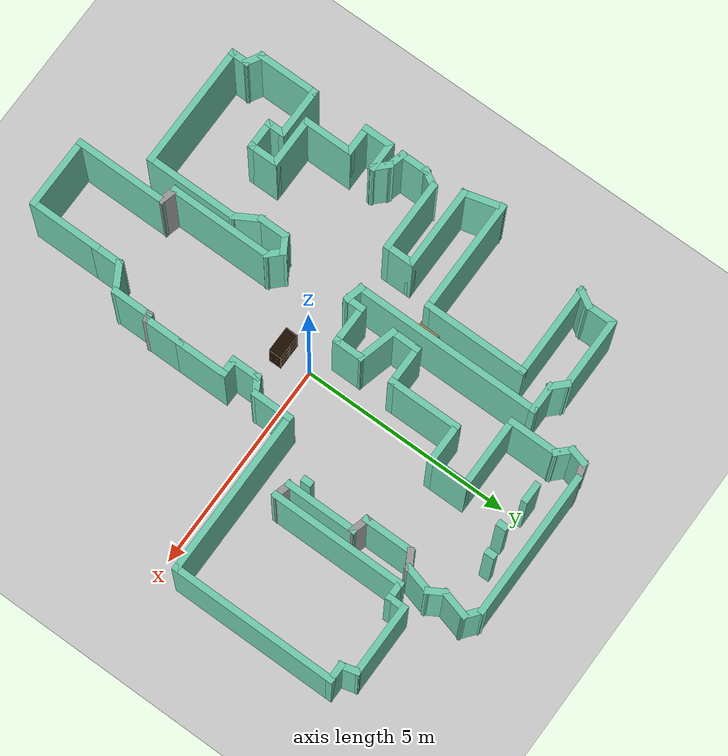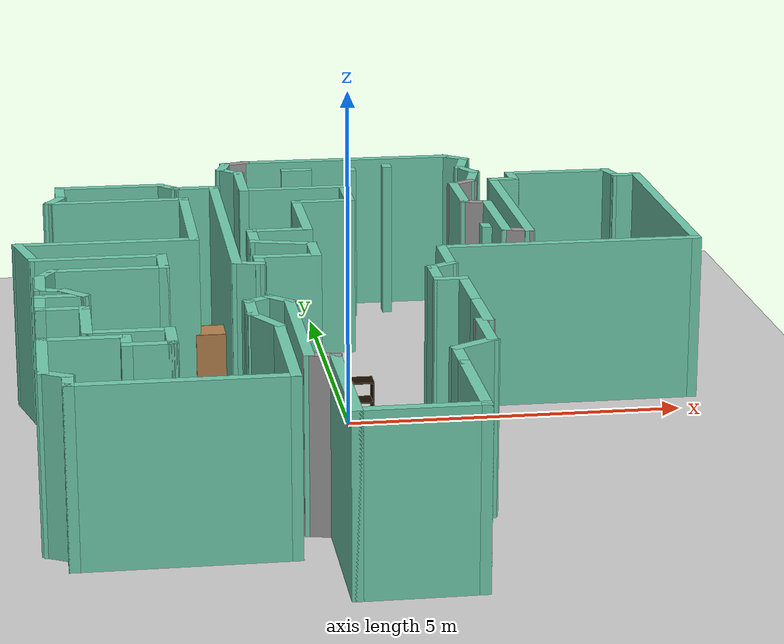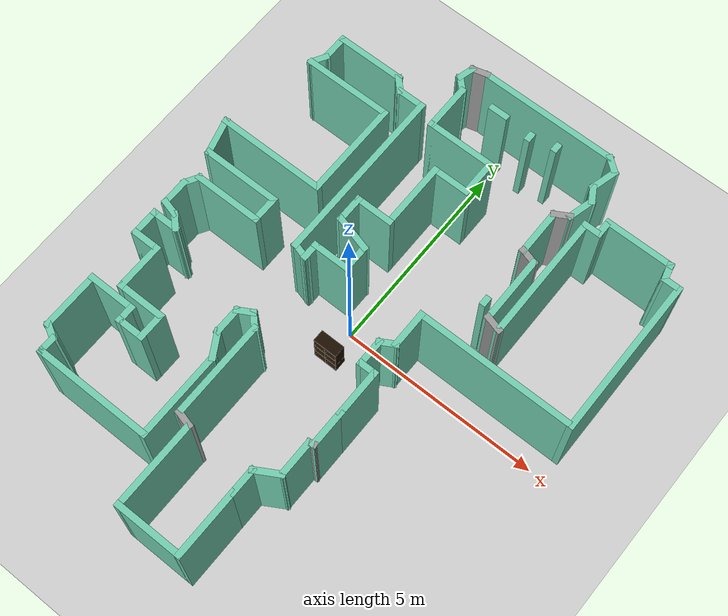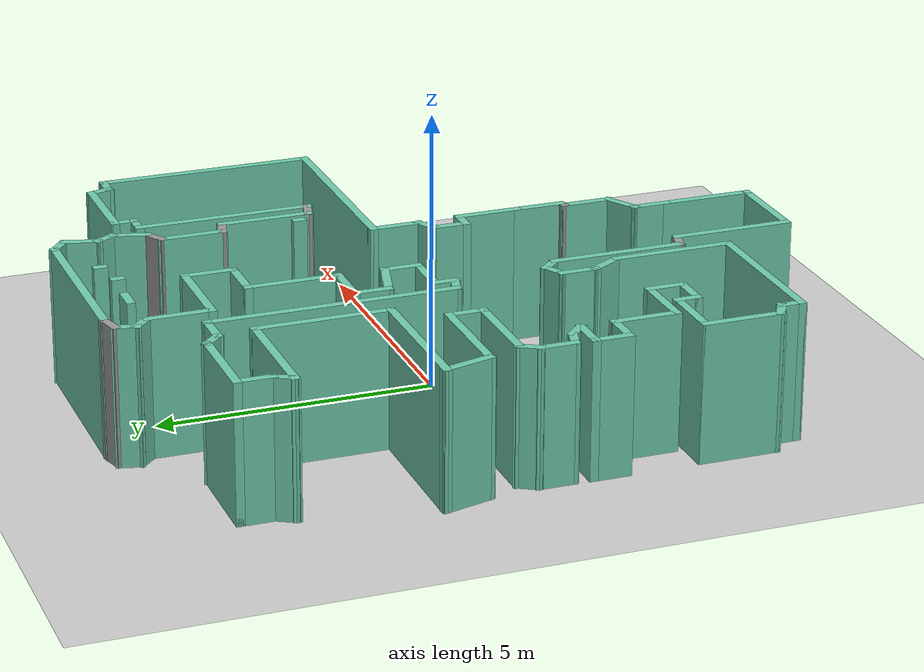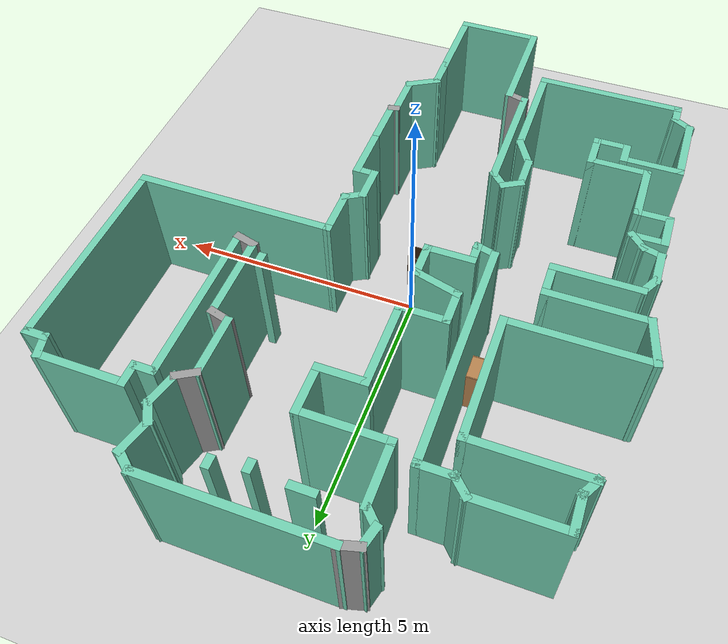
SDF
<sdf version="1.6">
 <world name="default">
  <light name="sun" type="directional">
   <pose>0 0 10 0 -0 0</pose>
   <diffuse>0.8 0.8 0.8 1</diffuse>
   <specular>0.2 0.2 0.2 1</specular>
   <attenuation>
    <range>1000</range>
    <constant>0.9</constant>
    <linear>0.01</linear>
    <quadratic>0.001</quadratic>
   </attenuation>
   <direction>-0.5 0.1 -0.9</direction>
  </light>
  <model name="ground_plane">
   <static>1</static>
   <link name="link">
    <collision name="collision">
     <geometry><plane><normal>0 0 1</normal><size>100 100</size></plane></geometry>
     <surface>
      <contact><collide_bitmask>65535</collide_bitmask></contact>
      <friction><ode><mu>100</mu><mu2>50</mu2></ode></friction>
     </surface>
    </collision>
    <visual name="visual">
     <cast_shadows>0</cast_shadows>
     <geometry><plane><normal>0 0 1</normal><size>100 100</size></plane></geometry>
     <material>
      <script><uri>file://media/materials/scripts/gazebo.material</uri><name>Gazebo/Grey</name></script>
     </material>
    </visual>
   </link>
  </model>
  <gravity>0 0 -9.8</gravity>
  <magnetic_field>6e-06 2.3e-05 -4.2e-05</magnetic_field>
  <atmosphere type="adiabatic"/>
  <physics name="default_physics" default="0" type="ode">
   <max_step_size>0.001</max_step_size>
   <real_time_factor>1</real_time_factor>
   <real_time_update_rate>1000</real_time_update_rate>
  </physics>
  <scene><ambient>0.4 0.4 0.4 1</ambient><background>0.7 0.7 0.7 1</background><shadows>1</shadows></scene>
  <audio><device>default</device></audio>
  <spherical_coordinates>
   <surface_model>EARTH_WGS84</surface_model>
   <latitude_deg>0</latitude_deg>
   <longitude_deg>0</longitude_deg>
   <elevation>0</elevation>
   <heading_deg>0</heading_deg>
  </spherical_coordinates>
  <model name="map_1">
   <pose>0.285268 -0.15484 0 0 -0 0</pose>
   <link name="Wall_1">
    <collision name="Wall_1_Collision">
     <geometry><box><size>3.5 0.15 2.5</size></box></geometry>
     <pose>0 0 1.25 0 -0 0</pose>
    </collision>
    <visual name="Wall_1_Visual">
     <pose>0 0 1.25 0 -0 0</pose>
     <geometry><box><size>3.5 0.15 2.5</size></box></geometry>
     <material>
      <script><uri>file://media/materials/scripts/gazebo.material</uri><name>Gazebo/Grey</name></script>
      <ambient>0.435294 0.796078 0.67451 1</ambient>
     </material>
     <meta><layer>0</layer></meta>
    </visual>
    <pose>0.433298 6.20572 0 0 -0 3.14159</pose>
   </link>
   <link name="Wall_10">
    <collision name="Wall_10_Collision">
     <geometry><box><size>1 0.15 2.5</size></box></geometry>
     <pose>0 0 1.25 0 -0 0</pose>
    </collision>
    <visual name="Wall_10_Visual">
     <pose>0 0 1.25 0 -0 0</pose>
     <geometry><box><size>1 0.15 2.5</size></box></geometry>
     <material>
      <script><uri>file://media/materials/scripts/gazebo.material</uri><name>Gazebo/Grey</name></script>
      <ambient>0.435294 0.796078 0.67451 1</ambient>
     </material>
     <meta><layer>0</layer></meta>
    </visual>
    <pose>-0.247875 3.57957 0 0 -0 3.14159</pose>
   </link>
   <link name="Wall_100">
    <collision name="Wall_100_Collision">
     <geometry><box><size>3.25 0.15 2.5</size></box></geometry>
     <pose>0 0 1.25 0 -0 0</pose>
    </collision>
    <visual name="Wall_100_Visual">
     <pose>0 0 1.25 0 -0 0</pose>
     <geometry><box><size>3.25 0.15 2.5</size></box></geometry>
     <material>
      <script><uri>file://media/materials/scripts/gazebo.material</uri><name>Gazebo/Grey</name></script>
      <ambient>0.435294 0.796078 0.67451 1</ambient>
     </material>
     <meta><layer>0</layer></meta>
    </visual>
    <pose>2.63867 3.00282 0 0 -0 -1.5708</pose>
   </link>
   <link name="Wall_101">
    <collision name="Wall_101_Collision">
     <geometry><box><size>0.5 0.15 2.5</size></box></geometry>
     <pose>0 0 1.25 0 -0 0</pose>
    </collision>
    <visual name="Wall_101_Visual">
     <pose>0 0 1.25 0 -0 0</pose>
     <geometry><box><size>0.5 0.15 2.5</size></box></geometry>
     <material>
      <script><uri>file://media/materials/scripts/gazebo.material</uri><name>Gazebo/Grey</name></script>
      <ambient>1 1 1 1</ambient>
     </material>
     <meta><layer>0</layer></meta>
    </visual>
    <pose>2.46963 1.49811 0 0 -0 2.87979</pose>
   </link>
   <link name="Wall_102">
    <collision name="Wall_102_Collision">
     <geometry><box><size>1.75 0.15 2.5</size></box></geometry>
     <pose>0 0 1.25 0 -0 0</pose>
    </collision>
    <visual name="Wall_102_Visual">
     <pose>0 0 1.25 0 -0 0</pose>
     <geometry><box><size>1.75 0.15 2.5</size></box></geometry>
     <material>
      <script><uri>file://media/materials/scripts/gazebo.material</uri><name>Gazebo/Grey</name></script>
      <ambient>0.435294 0.796078 0.67451 1</ambient>
     </material>
     <meta><layer>0</layer></meta>
    </visual>
    <pose>2.30059 2.3434 0 0 -0 1.5708</pose>
   </link>
   <link name="Wall_103">
    <collision name="Wall_103_Collision">
     <geometry><box><size>0.5 0.15 2.5</size></box></geometry>
     <pose>0 0 1.25 0 -0 0</pose>
    </collision>
    <visual name="Wall_103_Visual">
     <pose>0 0 1.25 0 -0 0</pose>
     <geometry><box><size>0.5 0.15 2.5</size></box></geometry>
     <material>
      <script><uri>file://media/materials/scripts/gazebo.material</uri><name>Gazebo/Grey</name></script>
      <ambient>1 1 1 1</ambient>
     </material>
     <meta><layer>0</layer></meta>
    </visual>
    <pose>2.13156 3.1887 0 0 -0 2.87979</pose>
   </link>
   <link name="Wall_104">
    <collision name="Wall_104_Collision">
     <geometry><box><size>1.25 0.15 2.5</size></box></geometry>
     <pose>0 0 1.25 0 -0 0</pose>
    </collision>
    <visual name="Wall_104_Visual">
     <pose>0 0 1.25 0 -0 0</pose>
     <geometry><box><size>1.25 0.15 2.5</size></box></geometry>
     <material>
      <script><uri>file://media/materials/scripts/gazebo.material</uri><name>Gazebo/Grey</name></script>
      <ambient>0.435294 0.796078 0.67451 1</ambient>
     </material>
     <meta><layer>0</layer></meta>
    </visual>
    <pose>1.96252 3.78399 0 0 -0 1.5708</pose>
   </link>
   <link name="Wall_105">
    <collision name="Wall_105_Collision">
     <geometry><box><size>0.5 0.15 2.5</size></box></geometry>
     <pose>0 0 1.25 0 -0 0</pose>
    </collision>
    <visual name="Wall_105_Visual">
     <pose>0 0 1.25 0 -0 0</pose>
     <geometry><box><size>0.5 0.15 2.5</size></box></geometry>
     <material>
      <script><uri>file://media/materials/scripts/gazebo.material</uri><name>Gazebo/Grey</name></script>
      <ambient>1 1 1 1</ambient>
     </material>
     <meta><layer>0</layer></meta>
    </visual>
    <pose>2.11407 4.42149 0 0 -0 0.523599</pose>
   </link>
   <link name="Wall_106">
    <collision name="Wall_106_Collision">
     <geometry><box><size>0.75 0.15 2.5</size></box></geometry>
     <pose>0 0 1.25 0 -0 0</pose>
    </collision>
    <visual name="Wall_106_Visual">
     <pose>0 0 1.25 0 -0 0</pose>
     <geometry><box><size>0.75 0.15 2.5</size></box></geometry>
     <material>
      <script><uri>file://media/materials/scripts/gazebo.material</uri><name>Gazebo/Grey</name></script>
      <ambient>0.435294 0.796078 0.67451 1</ambient>
     </material>
     <meta><layer>0</layer></meta>
    </visual>
    <pose>2.34327 4.79877 0 0 -0 1.309</pose>
   </link>
   <link name="Wall_107">
    <collision name="Wall_107_Collision">
     <geometry><box><size>0.5 0.15 2.5</size></box></geometry>
     <pose>0 0 1.25 0 -0 0</pose>
    </collision>
    <visual name="Wall_107_Visual">
     <pose>0 0 1.25 0 -0 0</pose>
     <geometry><box><size>0.5 0.15 2.5</size></box></geometry>
     <material>
      <script><uri>file://media/materials/scripts/gazebo.material</uri><name>Gazebo/Grey</name></script>
      <ambient>0.435294 0.796078 0.67451 1</ambient>
     </material>
     <meta><layer>0</layer></meta>
    </visual>
    <pose>2.33342 5.2401 0 0 -0 2.0944</pose>
   </link>
   <link name="Wall_108">
    <collision name="Wall_108_Collision">
     <geometry><box><size>0.75 0.15 2.5</size></box></geometry>
     <pose>0 0 1.25 0 -0 0</pose>
    </collision>
    <visual name="Wall_108_Visual">
     <pose>0 0 1.25 0 -0 0</pose>
     <geometry><box><size>0.75 0.15 2.5</size></box></geometry>
     <material>
      <script><uri>file://media/materials/scripts/gazebo.material</uri><name>Gazebo/Grey</name></script>
      <ambient>0.435294 0.796078 0.67451 1</ambient>
     </material>
     <meta><layer>0</layer></meta>
    </visual>
    <pose>2.32356 5.68143 0 0 -0 1.309</pose>
   </link>
   <link name="Wall_109">
    <collision name="Wall_109_Collision">
     <geometry><box><size>0.525223 0.15 2.5</size></box></geometry>
     <pose>0 0 1.25 0 -0 0</pose>
    </collision>
    <visual name="Wall_109_Visual">
     <pose>0 0 1.25 0 -0 0</pose>
     <geometry><box><size>0.525223 0.15 2.5</size></box></geometry>
     <material>
      <script><uri>file://media/materials/scripts/gazebo.material</uri><name>Gazebo/Grey</name></script>
      <ambient>0.435294 0.796078 0.67451 1</ambient>
     </material>
     <meta><layer>0</layer></meta>
    </visual>
    <pose>2.25475 6.08846 0 0 -0 2.46648</pose>
   </link>
   <link name="Wall_11">
    <collision name="Wall_11_Collision">
     <geometry><box><size>1.75 0.15 2.5</size></box></geometry>
     <pose>0 0 1.25 0 -0 0</pose>
    </collision>
    <visual name="Wall_11_Visual">
     <pose>0 0 1.25 0 -0 0</pose>
     <geometry><box><size>1.75 0.15 2.5</size></box></geometry>
     <material>
      <script><uri>file://media/materials/scripts/gazebo.material</uri><name>Gazebo/Grey</name></script>
      <ambient>0.435294 0.796078 0.67451 1</ambient>
     </material>
     <meta><layer>0</layer></meta>
    </visual>
    <pose>-0.672875 2.77957 0 0 -0 -1.5708</pose>
   </link>
   <link name="Wall_111">
    <collision name="Wall_111_Collision">
     <geometry><box><size>0.5 0.15 2.5</size></box></geometry>
     <pose>0 0 1.25 0 -0 0</pose>
    </collision>
    <visual name="Wall_111_Visual">
     <pose>0 0 1.25 0 -0 0</pose>
     <geometry><box><size>0.5 0.15 2.5</size></box></geometry>
     <material>
      <script><uri>file://media/materials/scripts/gazebo.material</uri><name>Gazebo/Grey</name></script>
      <ambient>0.435294 0.796078 0.67451 1</ambient>
     </material>
     <meta><layer>0</layer></meta>
    </visual>
    <pose>-0.451736 5.60255 0 0 -0 0</pose>
   </link>
   <link name="Wall_113">
    <collision name="Wall_113_Collision">
     <geometry><box><size>0.25 0.15 2.5</size></box></geometry>
     <pose>0 0 1.25 0 -0 0</pose>
    </collision>
    <visual name="Wall_113_Visual">
     <pose>0 0 1.25 0 -0 0</pose>
     <geometry><box><size>0.25 0.15 2.5</size></box></geometry>
     <material>
      <script><uri>file://media/materials/scripts/gazebo.material</uri><name>Gazebo/Grey</name></script>
      <ambient>0.435294 0.796078 0.67451 1</ambient>
     </material>
     <meta><layer>0</layer></meta>
    </visual>
    <pose>0.443922 5.53019 0 0 -0 1.5708</pose>
   </link>
   <link name="Wall_115">
    <collision name="Wall_115_Collision">
     <geometry><box><size>0.25 0.15 2.5</size></box></geometry>
     <pose>0 0 1.25 0 -0 0</pose>
    </collision>
    <visual name="Wall_115_Visual">
     <pose>0 0 1.25 0 -0 0</pose>
     <geometry><box><size>0.25 0.15 2.5</size></box></geometry>
     <material>
      <script><uri>file://media/materials/scripts/gazebo.material</uri><name>Gazebo/Grey</name></script>
      <ambient>0.435294 0.796078 0.67451 1</ambient>
     </material>
     <meta><layer>0</layer></meta>
    </visual>
    <pose>1.05573 5.67491 0 0 -0 -1.5708</pose>
   </link>
   <link name="Wall_117">
    <collision name="Wall_117_Collision">
     <geometry><box><size>0.25 0.15 2.5</size></box></geometry>
     <pose>0 0 1.25 0 -0 0</pose>
    </collision>
    <visual name="Wall_117_Visual">
     <pose>0 0 1.25 0 -0 0</pose>
     <geometry><box><size>0.25 0.15 2.5</size></box></geometry>
     <material>
      <script><uri>file://media/materials/scripts/gazebo.material</uri><name>Gazebo/Grey</name></script>
      <ambient>0.435294 0.796078 0.67451 1</ambient>
     </material>
     <meta><layer>0</layer></meta>
    </visual>
    <pose>2.03461 1.79818 0 0 -0 1.5708</pose>
   </link>
   <link name="Wall_12">
    <collision name="Wall_12_Collision">
     <geometry><box><size>1 0.15 2.5</size></box></geometry>
     <pose>0 0 1.25 0 -0 0</pose>
    </collision>
    <visual name="Wall_12_Visual">
     <pose>0 0 1.25 0 -0 0</pose>
     <geometry><box><size>1 0.15 2.5</size></box></geometry>
     <material>
      <script><uri>file://media/materials/scripts/gazebo.material</uri><name>Gazebo/Grey</name></script>
      <ambient>0.435294 0.796078 0.67451 1</ambient>
     </material>
     <meta><layer>0</layer></meta>
    </visual>
    <pose>-1.09787 1.97957 0 0 -0 3.14159</pose>
   </link>
   <link name="Wall_13">
    <collision name="Wall_13_Collision">
     <geometry><box><size>0.75 0.15 2.5</size></box></geometry>
     <pose>0 0 1.25 0 -0 0</pose>
    </collision>
    <visual name="Wall_13_Visual">
     <pose>0 0 1.25 0 -0 0</pose>
     <geometry><box><size>0.75 0.15 2.5</size></box></geometry>
     <material>
      <script><uri>file://media/materials/scripts/gazebo.material</uri><name>Gazebo/Grey</name></script>
      <ambient>0.435294 0.796078 0.67451 1</ambient>
     </material>
     <meta><layer>0</layer></meta>
    </visual>
    <pose>-1.52287 1.67957 0 0 -0 -1.5708</pose>
   </link>
   <link name="Wall_14">
    <collision name="Wall_14_Collision">
     <geometry><box><size>1 0.15 2.5</size></box></geometry>
     <pose>0 0 1.25 0 -0 0</pose>
    </collision>
    <visual name="Wall_14_Visual">
     <pose>0 0 1.25 0 -0 0</pose>
     <geometry><box><size>1 0.15 2.5</size></box></geometry>
     <material>
      <script><uri>file://media/materials/scripts/gazebo.material</uri><name>Gazebo/Grey</name></script>
      <ambient>0.435294 0.796078 0.67451 1</ambient>
     </material>
     <meta><layer>0</layer></meta>
    </visual>
    <pose>-1.11236 1.26957 0 0 -0 -0.261799</pose>
   </link>
   <link name="Wall_15">
    <collision name="Wall_15_Collision">
     <geometry><box><size>0.75 0.15 2.5</size></box></geometry>
     <pose>0 0 1.25 0 -0 0</pose>
    </collision>
    <visual name="Wall_15_Visual">
     <pose>0 0 1.25 0 -0 0</pose>
     <geometry><box><size>0.75 0.15 2.5</size></box></geometry>
     <material>
      <script><uri>file://media/materials/scripts/gazebo.material</uri><name>Gazebo/Grey</name></script>
      <ambient>0.435294 0.796078 0.67451 1</ambient>
     </material>
     <meta><layer>0</layer></meta>
    </visual>
    <pose>-0.701838 0.859574 0 0 -0 -1.5708</pose>
   </link>
   <link name="Wall_16">
    <collision name="Wall_16_Collision">
     <geometry><box><size>1 0.15 2.5</size></box></geometry>
     <pose>0 0 1.25 0 -0 0</pose>
    </collision>
    <visual name="Wall_16_Visual">
     <pose>0 0 1.25 0 -0 0</pose>
     <geometry><box><size>1 0.15 2.5</size></box></geometry>
     <material>
      <script><uri>file://media/materials/scripts/gazebo.material</uri><name>Gazebo/Grey</name></script>
      <ambient>0.435294 0.796078 0.67451 1</ambient>
     </material>
     <meta><layer>0</layer></meta>
    </visual>
    <pose>-1.12684 0.559574 0 0 -0 3.14159</pose>
   </link>
   <link name="Wall_2">
    <collision name="Wall_2_Collision">
     <geometry><box><size>0.5 0.15 2.5</size></box></geometry>
     <pose>0 0 1.25 0 -0 0</pose>
    </collision>
    <visual name="Wall_2_Visual">
     <pose>0 0 1.25 0 -0 0</pose>
     <geometry><box><size>0.5 0.15 2.5</size></box></geometry>
     <material>
      <script><uri>file://media/materials/scripts/gazebo.material</uri><name>Gazebo/Grey</name></script>
      <ambient>1 1 1 1</ambient>
     </material>
     <meta><layer>0</layer></meta>
    </visual>
    <pose>-1.41074 6.16043 0 0 -0 -2.87979</pose>
   </link>
   <link name="Wall_24">
    <collision name="Wall_24_Collision">
     <geometry><box><size>0.5 0.15 2.5</size></box></geometry>
     <pose>0 0 1.25 0 -0 0</pose>
    </collision>
    <visual name="Wall_24_Visual">
     <pose>0 0 1.25 0 -0 0</pose>
     <geometry><box><size>0.5 0.15 2.5</size></box></geometry>
     <material>
      <script><uri>file://media/materials/scripts/gazebo.material</uri><name>Gazebo/Grey</name></script>
      <ambient>0.435294 0.796078 0.67451 1</ambient>
     </material>
     <meta><layer>0</layer></meta>
    </visual>
    <pose>-1.55184 0.384574 0 0 -0 -1.5708</pose>
   </link>
   <link name="Wall_25">
    <collision name="Wall_25_Collision">
     <geometry><box><size>0.5 0.15 2.5</size></box></geometry>
     <pose>0 0 1.25 0 -0 0</pose>
    </collision>
    <visual name="Wall_25_Visual">
     <pose>0 0 1.25 0 -0 0</pose>
     <geometry><box><size>0.5 0.15 2.5</size></box></geometry>
     <material>
      <script><uri>file://media/materials/scripts/gazebo.material</uri><name>Gazebo/Grey</name></script>
      <ambient>0.435294 0.796078 0.67451 1</ambient>
     </material>
     <meta><layer>0</layer></meta>
    </visual>
    <pose>-1.72087 0.254867 0 0 -0 2.87979</pose>
   </link>
   <link name="Wall_28">
    <collision name="Wall_28_Collision">
     <geometry><box><size>4.5 0.15 2.5</size></box></geometry>
     <pose>0 0 1.25 0 -0 0</pose>
    </collision>
    <visual name="Wall_28_Visual">
     <pose>0 0 1.25 0 -0 0</pose>
     <geometry><box><size>4.5 0.15 2.5</size></box></geometry>
     <material>
      <script><uri>file://media/materials/scripts/gazebo.material</uri><name>Gazebo/Grey</name></script>
      <ambient>0.435294 0.796078 0.67451 1</ambient>
     </material>
     <meta><layer>0</layer></meta>
    </visual>
    <pose>-1.88991 2.47516 0 0 -0 1.5708</pose>
   </link>
   <link name="Wall_29">
    <collision name="Wall_29_Collision">
     <geometry><box><size>0.75 0.15 2.5</size></box></geometry>
     <pose>0 0 1.25 0 -0 0</pose>
    </collision>
    <visual name="Wall_29_Visual">
     <pose>0 0 1.25 0 -0 0</pose>
     <geometry><box><size>0.75 0.15 2.5</size></box></geometry>
     <material>
      <script><uri>file://media/materials/scripts/gazebo.material</uri><name>Gazebo/Grey</name></script>
      <ambient>0.435294 0.796078 0.67451 1</ambient>
     </material>
     <meta><layer>0</layer></meta>
    </visual>
    <pose>-2.18991 4.65016 0 0 -0 3.14159</pose>
   </link>
   <link name="Wall_3">
    <collision name="Wall_3_Collision">
     <geometry><box><size>0.5 0.15 2.5</size></box></geometry>
     <pose>0 0 1.25 0 -0 0</pose>
    </collision>
    <visual name="Wall_3_Visual">
     <pose>0 0 1.25 0 -0 0</pose>
     <geometry><box><size>0.5 0.15 2.5</size></box></geometry>
     <material>
      <script><uri>file://media/materials/scripts/gazebo.material</uri><name>Gazebo/Grey</name></script>
      <ambient>0.435294 0.796078 0.67451 1</ambient>
     </material>
     <meta><layer>0</layer></meta>
    </visual>
    <pose>-1.62507 5.94609 0 0 -0 -1.8326</pose>
   </link>
   <link name="Wall_30">
    <collision name="Wall_30_Collision">
     <geometry><box><size>0.5 0.15 2.5</size></box></geometry>
     <pose>0 0 1.25 0 -0 0</pose>
    </collision>
    <visual name="Wall_30_Visual">
     <pose>0 0 1.25 0 -0 0</pose>
     <geometry><box><size>0.5 0.15 2.5</size></box></geometry>
     <material>
      <script><uri>file://media/materials/scripts/gazebo.material</uri><name>Gazebo/Grey</name></script>
      <ambient>0.435294 0.796078 0.67451 1</ambient>
     </material>
     <meta><layer>0</layer></meta>
    </visual>
    <pose>-2.61366 4.7739 0 0 -0 2.35619</pose>
   </link>
   <link name="Wall_31">
    <collision name="Wall_31_Collision">
     <geometry><box><size>1.75 0.15 2.5</size></box></geometry>
     <pose>0 0 1.25 0 -0 0</pose>
    </collision>
    <visual name="Wall_31_Visual">
     <pose>0 0 1.25 0 -0 0</pose>
     <geometry><box><size>1.75 0.15 2.5</size></box></geometry>
     <material>
      <script><uri>file://media/materials/scripts/gazebo.material</uri><name>Gazebo/Grey</name></script>
      <ambient>0.435294 0.796078 0.67451 1</ambient>
     </material>
     <meta><layer>0</layer></meta>
    </visual>
    <pose>-3.5374 4.89765 0 0 -0 3.14159</pose>
   </link>
   <link name="Wall_32">
    <collision name="Wall_32_Collision">
     <geometry><box><size>0.75 0.15 2.5</size></box></geometry>
     <pose>0 0 1.25 0 -0 0</pose>
    </collision>
    <visual name="Wall_32_Visual">
     <pose>0 0 1.25 0 -0 0</pose>
     <geometry><box><size>0.75 0.15 2.5</size></box></geometry>
     <material>
      <script><uri>file://media/materials/scripts/gazebo.material</uri><name>Gazebo/Grey</name></script>
      <ambient>0.435294 0.796078 0.67451 1</ambient>
     </material>
     <meta><layer>0</layer></meta>
    </visual>
    <pose>-4.3374 4.59765 0 0 -0 -1.5708</pose>
   </link>
   <link name="Wall_33">
    <collision name="Wall_33_Collision">
     <geometry><box><size>0.5 0.15 2.5</size></box></geometry>
     <pose>0 0 1.25 0 -0 0</pose>
    </collision>
    <visual name="Wall_33_Visual">
     <pose>0 0 1.25 0 -0 0</pose>
     <geometry><box><size>0.5 0.15 2.5</size></box></geometry>
     <material>
      <script><uri>file://media/materials/scripts/gazebo.material</uri><name>Gazebo/Grey</name></script>
      <ambient>0.435294 0.796078 0.67451 1</ambient>
     </material>
     <meta><layer>0</layer></meta>
    </visual>
    <pose>-4.4249 4.14609 0 0 -0 -2.0944</pose>
   </link>
   <link name="Wall_37">
    <collision name="Wall_37_Collision">
     <geometry><box><size>2.25 0.15 2.5</size></box></geometry>
     <pose>0 0 1.25 0 -0 0</pose>
    </collision>
    <visual name="Wall_37_Visual">
     <pose>0 0 1.25 0 -0 0</pose>
     <geometry><box><size>2.25 0.15 2.5</size></box></geometry>
     <material>
      <script><uri>file://media/materials/scripts/gazebo.material</uri><name>Gazebo/Grey</name></script>
      <ambient>0.435294 0.796078 0.67451 1</ambient>
     </material>
     <meta><layer>0</layer></meta>
    </visual>
    <pose>-3.4624 3.99454 0 0 -0 0</pose>
   </link>
   <link name="Wall_38">
    <collision name="Wall_38_Collision">
     <geometry><box><size>2.5 0.15 2.5</size></box></geometry>
     <pose>0 0 1.25 0 -0 0</pose>
    </collision>
    <visual name="Wall_38_Visual">
     <pose>0 0 1.25 0 -0 0</pose>
     <geometry><box><size>2.5 0.15 2.5</size></box></geometry>
     <material>
      <script><uri>file://media/materials/scripts/gazebo.material</uri><name>Gazebo/Grey</name></script>
      <ambient>0.435294 0.796078 0.67451 1</ambient>
     </material>
     <meta><layer>0</layer></meta>
    </visual>
    <pose>-2.4124 2.81954 0 0 -0 -1.5708</pose>
   </link>
   <link name="Wall_39">
    <collision name="Wall_39_Collision">
     <geometry><box><size>2.75 0.15 2.5</size></box></geometry>
     <pose>0 0 1.25 0 -0 0</pose>
    </collision>
    <visual name="Wall_39_Visual">
     <pose>0 0 1.25 0 -0 0</pose>
     <geometry><box><size>2.75 0.15 2.5</size></box></geometry>
     <material>
      <script><uri>file://media/materials/scripts/gazebo.material</uri><name>Gazebo/Grey</name></script>
      <ambient>0.435294 0.796078 0.67451 1</ambient>
     </material>
     <meta><layer>0</layer></meta>
    </visual>
    <pose>-3.7124 1.64454 0 0 -0 3.14159</pose>
   </link>
   <link name="Wall_4">
    <collision name="Wall_4_Collision">
     <geometry><box><size>0.5 0.15 2.5</size></box></geometry>
     <pose>0 0 1.25 0 -0 0</pose>
    </collision>
    <visual name="Wall_4_Visual">
     <pose>0 0 1.25 0 -0 0</pose>
     <geometry><box><size>0.5 0.15 2.5</size></box></geometry>
     <material>
      <script><uri>file://media/materials/scripts/gazebo.material</uri><name>Gazebo/Grey</name></script>
      <ambient>0.435294 0.796078 0.67451 1</ambient>
     </material>
     <meta><layer>0</layer></meta>
    </visual>
    <pose>-1.54662 5.65331 0 0 -0 -0.785398</pose>
   </link>
   <link name="Wall_40">
    <collision name="Wall_40_Collision">
     <geometry><box><size>1 0.15 2.5</size></box></geometry>
     <pose>0 0 1.25 0 -0 0</pose>
    </collision>
    <visual name="Wall_40_Visual">
     <pose>0 0 1.25 0 -0 0</pose>
     <geometry><box><size>1 0.15 2.5</size></box></geometry>
     <material>
      <script><uri>file://media/materials/scripts/gazebo.material</uri><name>Gazebo/Grey</name></script>
      <ambient>0.435294 0.796078 0.67451 1</ambient>
     </material>
     <meta><layer>0</layer></meta>
    </visual>
    <pose>-4.9024 1.23402 0 0 -0 -1.309</pose>
   </link>
   <link name="Wall_41">
    <collision name="Wall_41_Collision">
     <geometry><box><size>2 0.15 2.5</size></box></geometry>
     <pose>0 0 1.25 0 -0 0</pose>
    </collision>
    <visual name="Wall_41_Visual">
     <pose>0 0 1.25 0 -0 0</pose>
     <geometry><box><size>2 0.15 2.5</size></box></geometry>
     <material>
      <script><uri>file://media/materials/scripts/gazebo.material</uri><name>Gazebo/Grey</name></script>
      <ambient>0.435294 0.796078 0.67451 1</ambient>
     </material>
     <meta><layer>0</layer></meta>
    </visual>
    <pose>-3.8674 0.823502 0 0 -0 0</pose>
   </link>
   <link name="Wall_42">
    <collision name="Wall_42_Collision">
     <geometry><box><size>0.75 0.15 2.5</size></box></geometry>
     <pose>0 0 1.25 0 -0 0</pose>
    </collision>
    <visual name="Wall_42_Visual">
     <pose>0 0 1.25 0 -0 0</pose>
     <geometry><box><size>0.75 0.15 2.5</size></box></geometry>
     <material>
      <script><uri>file://media/materials/scripts/gazebo.material</uri><name>Gazebo/Grey</name></script>
      <ambient>0.435294 0.796078 0.67451 1</ambient>
     </material>
     <meta><layer>0</layer></meta>
    </visual>
    <pose>-2.9424 0.523502 0 0 -0 -1.5708</pose>
   </link>
   <link name="Wall_43">
    <collision name="Wall_43_Collision">
     <geometry><box><size>1.75 0.15 2.5</size></box></geometry>
     <pose>0 0 1.25 0 -0 0</pose>
    </collision>
    <visual name="Wall_43_Visual">
     <pose>0 0 1.25 0 -0 0</pose>
     <geometry><box><size>1.75 0.15 2.5</size></box></geometry>
     <material>
      <script><uri>file://media/materials/scripts/gazebo.material</uri><name>Gazebo/Grey</name></script>
      <ambient>0.435294 0.796078 0.67451 1</ambient>
     </material>
     <meta><layer>0</layer></meta>
    </visual>
    <pose>-3.7424 0.223502 0 0 -0 3.14159</pose>
   </link>
   <link name="Wall_44">
    <collision name="Wall_44_Collision">
     <geometry><box><size>0.5 0.15 2.5</size></box></geometry>
     <pose>0 0 1.25 0 -0 0</pose>
    </collision>
    <visual name="Wall_44_Visual">
     <pose>0 0 1.25 0 -0 0</pose>
     <geometry><box><size>0.5 0.15 2.5</size></box></geometry>
     <material>
      <script><uri>file://media/materials/scripts/gazebo.material</uri><name>Gazebo/Grey</name></script>
      <ambient>0.435294 0.796078 0.67451 1</ambient>
     </material>
     <meta><layer>0</layer></meta>
    </visual>
    <pose>-4.6299 0.071948 0 0 -0 -2.0944</pose>
   </link>
   <link name="Wall_47">
    <collision name="Wall_47_Collision">
     <geometry><box><size>0.75 0.15 2.5</size></box></geometry>
     <pose>0 0 1.25 0 -0 0</pose>
    </collision>
    <visual name="Wall_47_Visual">
     <pose>0 0 1.25 0 -0 0</pose>
     <geometry><box><size>0.75 0.15 2.5</size></box></geometry>
     <material>
      <script><uri>file://media/materials/scripts/gazebo.material</uri><name>Gazebo/Grey</name></script>
      <ambient>0.435294 0.796078 0.67451 1</ambient>
     </material>
     <meta><layer>0</layer></meta>
    </visual>
    <pose>-4.7174 -0.379607 0 0 -0 -1.5708</pose>
   </link>
   <link name="Wall_48">
    <collision name="Wall_48_Collision">
     <geometry><box><size>0.5 0.15 2.5</size></box></geometry>
     <pose>0 0 1.25 0 -0 0</pose>
    </collision>
    <visual name="Wall_48_Visual">
     <pose>0 0 1.25 0 -0 0</pose>
     <geometry><box><size>0.5 0.15 2.5</size></box></geometry>
     <material>
      <script><uri>file://media/materials/scripts/gazebo.material</uri><name>Gazebo/Grey</name></script>
      <ambient>0.435294 0.796078 0.67451 1</ambient>
     </material>
     <meta><layer>0</layer></meta>
    </visual>
    <pose>-4.54837 -0.7249 0 0 -0 -0.261799</pose>
   </link>
   <link name="Wall_49">
    <collision name="Wall_49_Collision">
     <geometry><box><size>0.5 0.15 2.5</size></box></geometry>
     <pose>0 0 1.25 0 -0 0</pose>
    </collision>
    <visual name="Wall_49_Visual">
     <pose>0 0 1.25 0 -0 0</pose>
     <geometry><box><size>0.5 0.15 2.5</size></box></geometry>
     <material>
      <script><uri>file://media/materials/scripts/gazebo.material</uri><name>Gazebo/Grey</name></script>
      <ambient>0.435294 0.796078 0.67451 1</ambient>
     </material>
     <meta><layer>0</layer></meta>
    </visual>
    <pose>-4.25558 -0.893937 0 0 -0 -0.785398</pose>
   </link>
   <link name="Wall_50">
    <collision name="Wall_50_Collision">
     <geometry><box><size>0.75 0.15 2.5</size></box></geometry>
     <pose>0 0 1.25 0 -0 0</pose>
    </collision>
    <visual name="Wall_50_Visual">
     <pose>0 0 1.25 0 -0 0</pose>
     <geometry><box><size>0.75 0.15 2.5</size></box></geometry>
     <material>
      <script><uri>file://media/materials/scripts/gazebo.material</uri><name>Gazebo/Grey</name></script>
      <ambient>0.435294 0.796078 0.67451 1</ambient>
     </material>
     <meta><layer>0</layer></meta>
    </visual>
    <pose>-4.43184 -1.01768 0 0 -0 3.14159</pose>
   </link>
   <link name="Wall_51">
    <collision name="Wall_51_Collision">
     <geometry><box><size>0.75 0.15 2.5</size></box></geometry>
     <pose>0 0 1.25 0 -0 0</pose>
    </collision>
    <visual name="Wall_51_Visual">
     <pose>0 0 1.25 0 -0 0</pose>
     <geometry><box><size>0.75 0.15 2.5</size></box></geometry>
     <material>
      <script><uri>file://media/materials/scripts/gazebo.material</uri><name>Gazebo/Grey</name></script>
      <ambient>0.435294 0.796078 0.67451 1</ambient>
     </material>
     <meta><layer>0</layer></meta>
    </visual>
    <pose>-4.73184 -1.31768 0 0 -0 -1.5708</pose>
   </link>
   <link name="Wall_52">
    <collision name="Wall_52_Collision">
     <geometry><box><size>0.75 0.15 2.5</size></box></geometry>
     <pose>0 0 1.25 0 -0 0</pose>
    </collision>
    <visual name="Wall_52_Visual">
     <pose>0 0 1.25 0 -0 0</pose>
     <geometry><box><size>0.75 0.15 2.5</size></box></geometry>
     <material>
      <script><uri>file://media/materials/scripts/gazebo.material</uri><name>Gazebo/Grey</name></script>
      <ambient>0.435294 0.796078 0.67451 1</ambient>
     </material>
     <meta><layer>0</layer></meta>
    </visual>
    <pose>-4.43184 -1.61768 0 0 -0 0</pose>
   </link>
   <link name="Wall_53">
    <collision name="Wall_53_Collision">
     <geometry><box><size>1.25 0.15 2.5</size></box></geometry>
     <pose>0 0 1.25 0 -0 0</pose>
    </collision>
    <visual name="Wall_53_Visual">
     <pose>0 0 1.25 0 -0 0</pose>
     <geometry><box><size>1.25 0.15 2.5</size></box></geometry>
     <material>
      <script><uri>file://media/materials/scripts/gazebo.material</uri><name>Gazebo/Grey</name></script>
      <ambient>0.435294 0.796078 0.67451 1</ambient>
     </material>
     <meta><layer>0</layer></meta>
    </visual>
    <pose>-4.13184 -2.16768 0 0 -0 -1.5708</pose>
   </link>
   <link name="Wall_54">
    <collision name="Wall_54_Collision">
     <geometry><box><size>1.25 0.15 2.5</size></box></geometry>
     <pose>0 0 1.25 0 -0 0</pose>
    </collision>
    <visual name="Wall_54_Visual">
     <pose>0 0 1.25 0 -0 0</pose>
     <geometry><box><size>1.25 0.15 2.5</size></box></geometry>
     <material>
      <script><uri>file://media/materials/scripts/gazebo.material</uri><name>Gazebo/Grey</name></script>
      <ambient>0.435294 0.796078 0.67451 1</ambient>
     </material>
     <meta><layer>0</layer></meta>
    </visual>
    <pose>-3.58184 -2.71768 0 0 -0 0</pose>
   </link>
   <link name="Wall_56">
    <collision name="Wall_56_Collision">
     <geometry><box><size>0.75 0.15 2.5</size></box></geometry>
     <pose>0 0 1.25 0 -0 0</pose>
    </collision>
    <visual name="Wall_56_Visual">
     <pose>0 0 1.25 0 -0 0</pose>
     <geometry><box><size>0.75 0.15 2.5</size></box></geometry>
     <material>
      <script><uri>file://media/materials/scripts/gazebo.material</uri><name>Gazebo/Grey</name></script>
      <ambient>0.435294 0.796078 0.67451 1</ambient>
     </material>
     <meta><layer>0</layer></meta>
    </visual>
    <pose>-3.03184 -3.01768 0 0 -0 -1.5708</pose>
   </link>
   <link name="Wall_59">
    <collision name="Wall_59_Collision">
     <geometry><box><size>0.75 0.15 2.5</size></box></geometry>
     <pose>0 0 1.25 0 -0 0</pose>
    </collision>
    <visual name="Wall_59_Visual">
     <pose>0 0 1.25 0 -0 0</pose>
     <geometry><box><size>0.75 0.15 2.5</size></box></geometry>
     <material>
      <script><uri>file://media/materials/scripts/gazebo.material</uri><name>Gazebo/Grey</name></script>
      <ambient>0.435294 0.796078 0.67451 1</ambient>
     </material>
     <meta><layer>0</layer></meta>
    </visual>
    <pose>-3.33184 -3.31768 0 0 -0 3.14159</pose>
   </link>
   <link name="Wall_60">
    <collision name="Wall_60_Collision">
     <geometry><box><size>0.5 0.15 2.5</size></box></geometry>
     <pose>0 0 1.25 0 -0 0</pose>
    </collision>
    <visual name="Wall_60_Visual">
     <pose>0 0 1.25 0 -0 0</pose>
     <geometry><box><size>0.5 0.15 2.5</size></box></geometry>
     <material>
      <script><uri>file://media/materials/scripts/gazebo.material</uri><name>Gazebo/Grey</name></script>
      <ambient>0.435294 0.796078 0.67451 1</ambient>
     </material>
     <meta><layer>0</layer></meta>
    </visual>
    <pose>-3.63184 -3.14268 0 0 -0 1.5708</pose>
   </link>
   <link name="Wall_61">
    <collision name="Wall_61_Collision">
     <geometry><box><size>1.25 0.15 2.5</size></box></geometry>
     <pose>0 0 1.25 0 -0 0</pose>
    </collision>
    <visual name="Wall_61_Visual">
     <pose>0 0 1.25 0 -0 0</pose>
     <geometry><box><size>1.25 0.15 2.5</size></box></geometry>
     <material>
      <script><uri>file://media/materials/scripts/gazebo.material</uri><name>Gazebo/Grey</name></script>
      <ambient>0.435294 0.796078 0.67451 1</ambient>
     </material>
     <meta><layer>0</layer></meta>
    </visual>
    <pose>-4.18184 -2.96768 0 0 -0 3.14159</pose>
   </link>
   <link name="Wall_62">
    <collision name="Wall_62_Collision">
     <geometry><box><size>1.5 0.15 2.5</size></box></geometry>
     <pose>0 0 1.25 0 -0 0</pose>
    </collision>
    <visual name="Wall_62_Visual">
     <pose>0 0 1.25 0 -0 0</pose>
     <geometry><box><size>1.5 0.15 2.5</size></box></geometry>
     <material>
      <script><uri>file://media/materials/scripts/gazebo.material</uri><name>Gazebo/Grey</name></script>
      <ambient>0.435294 0.796078 0.67451 1</ambient>
     </material>
     <meta><layer>0</layer></meta>
    </visual>
    <pose>-4.73184 -3.64268 0 0 -0 -1.5708</pose>
   </link>
   <link name="Wall_63">
    <collision name="Wall_63_Collision">
     <geometry><box><size>0.5 0.15 2.5</size></box></geometry>
     <pose>0 0 1.25 0 -0 0</pose>
    </collision>
    <visual name="Wall_63_Visual">
     <pose>0 0 1.25 0 -0 0</pose>
     <geometry><box><size>0.5 0.15 2.5</size></box></geometry>
     <material>
      <script><uri>file://media/materials/scripts/gazebo.material</uri><name>Gazebo/Grey</name></script>
      <ambient>0.435294 0.796078 0.67451 1</ambient>
     </material>
     <meta><layer>0</layer></meta>
    </visual>
    <pose>-4.58029 -4.40518 0 0 -0 -0.523599</pose>
   </link>
   <link name="Wall_64">
    <collision name="Wall_64_Collision">
     <geometry><box><size>0.5 0.15 2.5</size></box></geometry>
     <pose>0 0 1.25 0 -0 0</pose>
    </collision>
    <visual name="Wall_64_Visual">
     <pose>0 0 1.25 0 -0 0</pose>
     <geometry><box><size>0.5 0.15 2.5</size></box></geometry>
     <material>
      <script><uri>file://media/materials/scripts/gazebo.material</uri><name>Gazebo/Grey</name></script>
      <ambient>0.435294 0.796078 0.67451 1</ambient>
     </material>
     <meta><layer>0</layer></meta>
    </visual>
    <pose>-4.42873 -4.66768 0 0 -0 -1.5708</pose>
   </link>
   <link name="Wall_65">
    <collision name="Wall_65_Collision">
     <geometry><box><size>3 0.15 2.5</size></box></geometry>
     <pose>0 0 1.25 0 -0 0</pose>
    </collision>
    <visual name="Wall_65_Visual">
     <pose>0 0 1.25 0 -0 0</pose>
     <geometry><box><size>3 0.15 2.5</size></box></geometry>
     <material>
      <script><uri>file://media/materials/scripts/gazebo.material</uri><name>Gazebo/Grey</name></script>
      <ambient>0.435294 0.796078 0.67451 1</ambient>
     </material>
     <meta><layer>0</layer></meta>
    </visual>
    <pose>-3.00373 -4.84268 0 0 -0 0</pose>
   </link>
   <link name="Wall_66">
    <collision name="Wall_66_Collision">
     <geometry><box><size>2.25 0.15 2.5</size></box></geometry>
     <pose>0 0 1.25 0 -0 0</pose>
    </collision>
    <visual name="Wall_66_Visual">
     <pose>0 0 1.25 0 -0 0</pose>
     <geometry><box><size>2.25 0.15 2.5</size></box></geometry>
     <material>
      <script><uri>file://media/materials/scripts/gazebo.material</uri><name>Gazebo/Grey</name></script>
      <ambient>0.435294 0.796078 0.67451 1</ambient>
     </material>
     <meta><layer>0</layer></meta>
    </visual>
    <pose>-1.57873 -3.79268 0 0 -0 1.5708</pose>
   </link>
   <link name="Wall_67">
    <collision name="Wall_67_Collision">
     <geometry><box><size>0.75 0.15 2.5</size></box></geometry>
     <pose>0 0 1.25 0 -0 0</pose>
    </collision>
    <visual name="Wall_67_Visual">
     <pose>0 0 1.25 0 -0 0</pose>
     <geometry><box><size>0.75 0.15 2.5</size></box></geometry>
     <material>
      <script><uri>file://media/materials/scripts/gazebo.material</uri><name>Gazebo/Grey</name></script>
      <ambient>0.435294 0.796078 0.67451 1</ambient>
     </material>
     <meta><layer>0</layer></meta>
    </visual>
    <pose>-1.72873 -2.48287 0 0 -0 2.0944</pose>
   </link>
   <link name="Wall_68">
    <collision name="Wall_68_Collision">
     <geometry><box><size>0.75 0.15 2.5</size></box></geometry>
     <pose>0 0 1.25 0 -0 0</pose>
    </collision>
    <visual name="Wall_68_Visual">
     <pose>0 0 1.25 0 -0 0</pose>
     <geometry><box><size>0.75 0.15 2.5</size></box></geometry>
     <material>
      <script><uri>file://media/materials/scripts/gazebo.material</uri><name>Gazebo/Grey</name></script>
      <ambient>0.435294 0.796078 0.67451 1</ambient>
     </material>
     <meta><layer>0</layer></meta>
    </visual>
    <pose>-1.87873 -1.92307 0 0 -0 1.5708</pose>
   </link>
   <link name="Wall_69">
    <collision name="Wall_69_Collision">
     <geometry><box><size>0.5 0.15 2.5</size></box></geometry>
     <pose>0 0 1.25 0 -0 0</pose>
    </collision>
    <visual name="Wall_69_Visual">
     <pose>0 0 1.25 0 -0 0</pose>
     <geometry><box><size>0.5 0.15 2.5</size></box></geometry>
     <material>
      <script><uri>file://media/materials/scripts/gazebo.material</uri><name>Gazebo/Grey</name></script>
      <ambient>0.435294 0.796078 0.67451 1</ambient>
     </material>
     <meta><layer>0</layer></meta>
    </visual>
    <pose>-1.72718 -1.53557 0 0 -0 0.523599</pose>
   </link>
   <link name="Wall_7">
    <collision name="Wall_7_Collision">
     <geometry><box><size>1.25 0.15 2.5</size></box></geometry>
     <pose>0 0 1.25 0 -0 0</pose>
    </collision>
    <visual name="Wall_7_Visual">
     <pose>0 0 1.25 0 -0 0</pose>
     <geometry><box><size>1.25 0.15 2.5</size></box></geometry>
     <material>
      <script><uri>file://media/materials/scripts/gazebo.material</uri><name>Gazebo/Grey</name></script>
      <ambient>0.435294 0.796078 0.67451 1</ambient>
     </material>
     <meta><layer>0</layer></meta>
    </visual>
    <pose>-1.42287 4.97957 0 0 -0 -1.5708</pose>
   </link>
   <link name="Wall_70">
    <collision name="Wall_70_Collision">
     <geometry><box><size>0.5 0.15 2.5</size></box></geometry>
     <pose>0 0 1.25 0 -0 0</pose>
    </collision>
    <visual name="Wall_70_Visual">
     <pose>0 0 1.25 0 -0 0</pose>
     <geometry><box><size>0.5 0.15 2.5</size></box></geometry>
     <material>
      <script><uri>file://media/materials/scripts/gazebo.material</uri><name>Gazebo/Grey</name></script>
      <ambient>0.435294 0.796078 0.67451 1</ambient>
     </material>
     <meta><layer>0</layer></meta>
    </visual>
    <pose>-1.45188 -1.57181 0 0 -0 -0.785398</pose>
   </link>
   <link name="Wall_71">
    <collision name="Wall_71_Collision">
     <geometry><box><size>2.5 0.15 2.5</size></box></geometry>
     <pose>0 0 1.25 0 -0 0</pose>
    </collision>
    <visual name="Wall_71_Visual">
     <pose>0 0 1.25 0 -0 0</pose>
     <geometry><box><size>2.5 0.15 2.5</size></box></geometry>
     <material>
      <script><uri>file://media/materials/scripts/gazebo.material</uri><name>Gazebo/Grey</name></script>
      <ambient>0.435294 0.796078 0.67451 1</ambient>
     </material>
     <meta><layer>0</layer></meta>
    </visual>
    <pose>-1.32814 -2.87055 0 0 -0 -1.5708</pose>
   </link>
   <link name="Wall_72">
    <collision name="Wall_72_Collision">
     <geometry><box><size>0.5 0.15 2.5</size></box></geometry>
     <pose>0 0 1.25 0 -0 0</pose>
    </collision>
    <visual name="Wall_72_Visual">
     <pose>0 0 1.25 0 -0 0</pose>
     <geometry><box><size>0.5 0.15 2.5</size></box></geometry>
     <material>
      <script><uri>file://media/materials/scripts/gazebo.material</uri><name>Gazebo/Grey</name></script>
      <ambient>1 1 1 1</ambient>
     </material>
     <meta><layer>0</layer></meta>
    </visual>
    <pose>-1.1591 -4.09085 0 0 -0 -0.261799</pose>
   </link>
   <link name="Wall_73">
    <collision name="Wall_73_Collision">
     <geometry><box><size>2.25 0.15 2.5</size></box></geometry>
     <pose>0 0 1.25 0 -0 0</pose>
    </collision>
    <visual name="Wall_73_Visual">
     <pose>0 0 1.25 0 -0 0</pose>
     <geometry><box><size>2.25 0.15 2.5</size></box></geometry>
     <material>
      <script><uri>file://media/materials/scripts/gazebo.material</uri><name>Gazebo/Grey</name></script>
      <ambient>0.435294 0.796078 0.67451 1</ambient>
     </material>
     <meta><layer>0</layer></meta>
    </visual>
    <pose>-0.990063 -5.18614 0 0 -0 -1.5708</pose>
   </link>
   <link name="Wall_74">
    <collision name="Wall_74_Collision">
     <geometry><box><size>1.75 0.15 2.5</size></box></geometry>
     <pose>0 0 1.25 0 -0 0</pose>
    </collision>
    <visual name="Wall_74_Visual">
     <pose>0 0 1.25 0 -0 0</pose>
     <geometry><box><size>1.75 0.15 2.5</size></box></geometry>
     <material>
      <script><uri>file://media/materials/scripts/gazebo.material</uri><name>Gazebo/Grey</name></script>
      <ambient>0.435294 0.796078 0.67451 1</ambient>
     </material>
     <meta><layer>0</layer></meta>
    </visual>
    <pose>-0.190062 -6.23614 0 0 -0 0</pose>
   </link>
   <link name="Wall_75">
    <collision name="Wall_75_Collision">
     <geometry><box><size>1.75 0.15 2.5</size></box></geometry>
     <pose>0 0 1.25 0 -0 0</pose>
    </collision>
    <visual name="Wall_75_Visual">
     <pose>0 0 1.25 0 -0 0</pose>
     <geometry><box><size>1.75 0.15 2.5</size></box></geometry>
     <material>
      <script><uri>file://media/materials/scripts/gazebo.material</uri><name>Gazebo/Grey</name></script>
      <ambient>0.435294 0.796078 0.67451 1</ambient>
     </material>
     <meta><layer>0</layer></meta>
    </visual>
    <pose>0.609937 -5.43614 0 0 -0 1.5708</pose>
   </link>
   <link name="Wall_76">
    <collision name="Wall_76_Collision">
     <geometry><box><size>0.75 0.15 2.5</size></box></geometry>
     <pose>0 0 1.25 0 -0 0</pose>
    </collision>
    <visual name="Wall_76_Visual">
     <pose>0 0 1.25 0 -0 0</pose>
     <geometry><box><size>0.75 0.15 2.5</size></box></geometry>
     <material>
      <script><uri>file://media/materials/scripts/gazebo.material</uri><name>Gazebo/Grey</name></script>
      <ambient>0.435294 0.796078 0.67451 1</ambient>
     </material>
     <meta><layer>0</layer></meta>
    </visual>
    <pose>0.609937 -4.33614 0 0 -0 1.5708</pose>
   </link>
   <link name="Wall_77">
    <collision name="Wall_77_Collision">
     <geometry><box><size>0.75 0.15 2.5</size></box></geometry>
     <pose>0 0 1.25 0 -0 0</pose>
    </collision>
    <visual name="Wall_77_Visual">
     <pose>0 0 1.25 0 -0 0</pose>
     <geometry><box><size>0.75 0.15 2.5</size></box></geometry>
     <material>
      <script><uri>file://media/materials/scripts/gazebo.material</uri><name>Gazebo/Grey</name></script>
      <ambient>0.435294 0.796078 0.67451 1</ambient>
     </material>
     <meta><layer>0</layer></meta>
    </visual>
    <pose>0.869745 -3.88614 0 0 -0 0.523599</pose>
   </link>
   <link name="Wall_78">
    <collision name="Wall_78_Collision">
     <geometry><box><size>1 0.15 2.5</size></box></geometry>
     <pose>0 0 1.25 0 -0 0</pose>
    </collision>
    <visual name="Wall_78_Visual">
     <pose>0 0 1.25 0 -0 0</pose>
     <geometry><box><size>1 0.15 2.5</size></box></geometry>
     <material>
      <script><uri>file://media/materials/scripts/gazebo.material</uri><name>Gazebo/Grey</name></script>
      <ambient>0.435294 0.796078 0.67451 1</ambient>
     </material>
     <meta><layer>0</layer></meta>
    </visual>
    <pose>1.12955 -3.31114 0 0 -0 1.5708</pose>
   </link>
   <link name="Wall_79">
    <collision name="Wall_79_Collision">
     <geometry><box><size>0.25 0.15 2.5</size></box></geometry>
     <pose>0 0 1.25 0 -0 0</pose>
    </collision>
    <visual name="Wall_79_Visual">
     <pose>0 0 1.25 0 -0 0</pose>
     <geometry><box><size>0.25 0.15 2.5</size></box></geometry>
     <material>
      <script><uri>file://media/materials/scripts/gazebo.material</uri><name>Gazebo/Grey</name></script>
      <ambient>1 1 1 1</ambient>
     </material>
     <meta><layer>0</layer></meta>
    </visual>
    <pose>1.17785 -2.8732 0 0 -0 0.261799</pose>
   </link>
   <link name="Wall_8">
    <collision name="Wall_8_Collision">
     <geometry><box><size>1.75 0.15 2.5</size></box></geometry>
     <pose>0 0 1.25 0 -0 0</pose>
    </collision>
    <visual name="Wall_8_Visual">
     <pose>0 0 1.25 0 -0 0</pose>
     <geometry><box><size>1.75 0.15 2.5</size></box></geometry>
     <material>
      <script><uri>file://media/materials/scripts/gazebo.material</uri><name>Gazebo/Grey</name></script>
      <ambient>0.435294 0.796078 0.67451 1</ambient>
     </material>
     <meta><layer>0</layer></meta>
    </visual>
    <pose>-0.622875 4.42957 0 0 -0 0</pose>
   </link>
   <link name="Wall_80">
    <collision name="Wall_80_Collision">
     <geometry><box><size>1 0.15 2.5</size></box></geometry>
     <pose>0 0 1.25 0 -0 0</pose>
    </collision>
    <visual name="Wall_80_Visual">
     <pose>0 0 1.25 0 -0 0</pose>
     <geometry><box><size>1 0.15 2.5</size></box></geometry>
     <material>
      <script><uri>file://media/materials/scripts/gazebo.material</uri><name>Gazebo/Grey</name></script>
      <ambient>0.435294 0.796078 0.67451 1</ambient>
     </material>
     <meta><layer>0</layer></meta>
    </visual>
    <pose>1.22615 -2.43526 0 0 -0 1.5708</pose>
   </link>
   <link name="Wall_81">
    <collision name="Wall_81_Collision">
     <geometry><box><size>1.25 0.15 2.5</size></box></geometry>
     <pose>0 0 1.25 0 -0 0</pose>
    </collision>
    <visual name="Wall_81_Visual">
     <pose>0 0 1.25 0 -0 0</pose>
     <geometry><box><size>1.25 0.15 2.5</size></box></geometry>
     <material>
      <script><uri>file://media/materials/scripts/gazebo.material</uri><name>Gazebo/Grey</name></script>
      <ambient>0.435294 0.796078 0.67451 1</ambient>
     </material>
     <meta><layer>0</layer></meta>
    </visual>
    <pose>1.22615 -1.46026 0 0 -0 1.5708</pose>
   </link>
   <link name="Wall_82">
    <collision name="Wall_82_Collision">
     <geometry><box><size>0.5 0.15 2.5</size></box></geometry>
     <pose>0 0 1.25 0 -0 0</pose>
    </collision>
    <visual name="Wall_82_Visual">
     <pose>0 0 1.25 0 -0 0</pose>
     <geometry><box><size>0.5 0.15 2.5</size></box></geometry>
     <material>
      <script><uri>file://media/materials/scripts/gazebo.material</uri><name>Gazebo/Grey</name></script>
      <ambient>0.435294 0.796078 0.67451 1</ambient>
     </material>
     <meta><layer>0</layer></meta>
    </visual>
    <pose>1.05114 -0.910258 0 0 -0 3.14159</pose>
   </link>
   <link name="Wall_83">
    <collision name="Wall_83_Collision">
     <geometry><box><size>0.75 0.15 2.5</size></box></geometry>
     <pose>0 0 1.25 0 -0 0</pose>
    </collision>
    <visual name="Wall_83_Visual">
     <pose>0 0 1.25 0 -0 0</pose>
     <geometry><box><size>0.75 0.15 2.5</size></box></geometry>
     <material>
      <script><uri>file://media/materials/scripts/gazebo.material</uri><name>Gazebo/Grey</name></script>
      <ambient>0.435294 0.796078 0.67451 1</ambient>
     </material>
     <meta><layer>0</layer></meta>
    </visual>
    <pose>0.876145 -0.610258 0 0 -0 1.5708</pose>
   </link>
   <link name="Wall_88">
    <collision name="Wall_88_Collision">
     <geometry><box><size>0.5 0.15 2.5</size></box></geometry>
     <pose>0 0 1.25 0 -0 0</pose>
    </collision>
    <visual name="Wall_88_Visual">
     <pose>0 0 1.25 0 -0 0</pose>
     <geometry><box><size>0.5 0.15 2.5</size></box></geometry>
     <material>
      <script><uri>file://media/materials/scripts/gazebo.material</uri><name>Gazebo/Grey</name></script>
      <ambient>0.435294 0.796078 0.67451 1</ambient>
     </material>
     <meta><layer>0</layer></meta>
    </visual>
    <pose>1.0277 -0.222758 0 0 -0 0.523599</pose>
   </link>
   <link name="Wall_9">
    <collision name="Wall_9_Collision">
     <geometry><box><size>1 0.15 2.5</size></box></geometry>
     <pose>0 0 1.25 0 -0 0</pose>
    </collision>
    <visual name="Wall_9_Visual">
     <pose>0 0 1.25 0 -0 0</pose>
     <geometry><box><size>1 0.15 2.5</size></box></geometry>
     <material>
      <script><uri>file://media/materials/scripts/gazebo.material</uri><name>Gazebo/Grey</name></script>
      <ambient>0.435294 0.796078 0.67451 1</ambient>
     </material>
     <meta><layer>0</layer></meta>
    </visual>
    <pose>0.177125 4.00457 0 0 -0 -1.5708</pose>
   </link>
   <link name="Wall_92">
    <collision name="Wall_92_Collision">
     <geometry><box><size>1 0.15 2.5</size></box></geometry>
     <pose>0 0 1.25 0 -0 0</pose>
    </collision>
    <visual name="Wall_92_Visual">
     <pose>0 0 1.25 0 -0 0</pose>
     <geometry><box><size>1 0.15 2.5</size></box></geometry>
     <material>
      <script><uri>file://media/materials/scripts/gazebo.material</uri><name>Gazebo/Grey</name></script>
      <ambient>0.435294 0.796078 0.67451 1</ambient>
     </material>
     <meta><layer>0</layer></meta>
    </visual>
    <pose>1.17925 0.289742 0 0 -0 1.5708</pose>
   </link>
   <link name="Wall_93">
    <collision name="Wall_93_Collision">
     <geometry><box><size>4 0.15 2.5</size></box></geometry>
     <pose>0 0 1.25 0 -0 0</pose>
    </collision>
    <visual name="Wall_93_Visual">
     <pose>0 0 1.25 0 -0 0</pose>
     <geometry><box><size>4 0.15 2.5</size></box></geometry>
     <material>
      <script><uri>file://media/materials/scripts/gazebo.material</uri><name>Gazebo/Grey</name></script>
      <ambient>0.435294 0.796078 0.67451 1</ambient>
     </material>
     <meta><layer>0</layer></meta>
    </visual>
    <pose>3.10425 0.714742 0 0 -0 0</pose>
   </link>
   <link name="Wall_94">
    <collision name="Wall_94_Collision">
     <geometry><box><size>4 0.15 2.5</size></box></geometry>
     <pose>0 0 1.25 0 -0 0</pose>
    </collision>
    <visual name="Wall_94_Visual">
     <pose>0 0 1.25 0 -0 0</pose>
     <geometry><box><size>4 0.15 2.5</size></box></geometry>
     <material>
      <script><uri>file://media/materials/scripts/gazebo.material</uri><name>Gazebo/Grey</name></script>
      <ambient>0.435294 0.796078 0.67451 1</ambient>
     </material>
     <meta><layer>0</layer></meta>
    </visual>
    <pose>5.02925 2.63974 0 0 -0 1.5708</pose>
   </link>
   <link name="Wall_95">
    <collision name="Wall_95_Collision">
     <geometry><box><size>0.5 0.15 2.5</size></box></geometry>
     <pose>0 0 1.25 0 -0 0</pose>
    </collision>
    <visual name="Wall_95_Visual">
     <pose>0 0 1.25 0 -0 0</pose>
     <geometry><box><size>0.5 0.15 2.5</size></box></geometry>
     <material>
      <script><uri>file://media/materials/scripts/gazebo.material</uri><name>Gazebo/Grey</name></script>
      <ambient>0.435294 0.796078 0.67451 1</ambient>
     </material>
     <meta><layer>0</layer></meta>
    </visual>
    <pose>4.85425 4.56474 0 0 -0 3.14159</pose>
   </link>
   <link name="Wall_96">
    <collision name="Wall_96_Collision">
     <geometry><box><size>0.5 0.15 2.5</size></box></geometry>
     <pose>0 0 1.25 0 -0 0</pose>
    </collision>
    <visual name="Wall_96_Visual">
     <pose>0 0 1.25 0 -0 0</pose>
     <geometry><box><size>0.5 0.15 2.5</size></box></geometry>
     <material>
      <script><uri>file://media/materials/scripts/gazebo.material</uri><name>Gazebo/Grey</name></script>
      <ambient>0.435294 0.796078 0.67451 1</ambient>
     </material>
     <meta><layer>0</layer></meta>
    </visual>
    <pose>4.63396 4.73378 0 0 -0 1.8326</pose>
   </link>
   <link name="Wall_97">
    <collision name="Wall_97_Collision">
     <geometry><box><size>1.75 0.15 2.5</size></box></geometry>
     <pose>0 0 1.25 0 -0 0</pose>
    </collision>
    <visual name="Wall_97_Visual">
     <pose>0 0 1.25 0 -0 0</pose>
     <geometry><box><size>1.75 0.15 2.5</size></box></geometry>
     <material>
      <script><uri>file://media/materials/scripts/gazebo.material</uri><name>Gazebo/Grey</name></script>
      <ambient>0.435294 0.796078 0.67451 1</ambient>
     </material>
     <meta><layer>0</layer></meta>
    </visual>
    <pose>3.78867 4.90282 0 0 -0 3.14159</pose>
   </link>
   <link name="Wall_98">
    <collision name="Wall_98_Collision">
     <geometry><box><size>0.5 0.15 2.5</size></box></geometry>
     <pose>0 0 1.25 0 -0 0</pose>
    </collision>
    <visual name="Wall_98_Visual">
     <pose>0 0 1.25 0 -0 0</pose>
     <geometry><box><size>0.5 0.15 2.5</size></box></geometry>
     <material>
      <script><uri>file://media/materials/scripts/gazebo.material</uri><name>Gazebo/Grey</name></script>
      <ambient>0.435294 0.796078 0.67451 1</ambient>
     </material>
     <meta><layer>0</layer></meta>
    </visual>
    <pose>2.98867 4.72782 0 0 -0 -1.5708</pose>
   </link>
   <link name="Wall_99">
    <collision name="Wall_99_Collision">
     <geometry><box><size>0.5 0.15 2.5</size></box></geometry>
     <pose>0 0 1.25 0 -0 0</pose>
    </collision>
    <visual name="Wall_99_Visual">
     <pose>0 0 1.25 0 -0 0</pose>
     <geometry><box><size>0.5 0.15 2.5</size></box></geometry>
     <material>
      <script><uri>file://media/materials/scripts/gazebo.material</uri><name>Gazebo/Grey</name></script>
      <ambient>0.435294 0.796078 0.67451 1</ambient>
     </material>
     <meta><layer>0</layer></meta>
    </visual>
    <pose>2.81367 4.55282 0 0 -0 3.14159</pose>
   </link>
   <static>1</static>
  </model>
  <model name="6方格书柜">
   <link name="Wall_0">
    <pose>0 0 0.01 0 -0 0</pose>
    <inertial>
     <mass>1.6201</mass>
     <inertia><ixx>0.0119</ixx><iyy>0.0631</iyy><izz>0.0513</izz><ixy>0</ixy><ixz>0</ixz><iyz>0</iyz></inertia>
    </inertial>
    <collision name="Wall_0_Collision"><geometry><box><size>0.616 0.296 0.02</size></box></geometry></collision>
    <visual name="Wall_0_Visual">
     <geometry><box><size>0.616 0.296 0.02</size></box></geometry>
     <material>
      <script><uri>file://media/materials/scripts/gazebo.material</uri><name>Gazebo/Grey</name></script>
      <ambient>0.105882 0.0509804 0 1</ambient>
     </material>
    </visual>
   </link>
   <joint name="0_2" type="fixed">
    <pose>-0.308 0 0 0 -0 0</pose>
    <parent>Wall_2</parent>
    <child>Wall_0</child>
    <axis>
     <xyz>1 0 0</xyz>
     <use_parent_model_frame>0</use_parent_model_frame>
     <limit><lower>-1e+16</lower><upper>1e+16</upper></limit>
    </axis>
   </joint>
   <joint name="0_12" type="fixed">
    <parent>Wall_12</parent>
    <child>Wall_0</child>
    <axis>
     <xyz>0 0 1</xyz>
     <use_parent_model_frame>0</use_parent_model_frame>
     <limit><lower>-1e+16</lower><upper>1e+16</upper></limit>
    </axis>
   </joint>
   <joint name="0_4" type="fixed">
    <pose>0.308 0 0 0 -0 0</pose>
    <parent>Wall_4</parent>
    <child>Wall_0</child>
    <axis>
     <xyz>1 0 0</xyz>
     <use_parent_model_frame>0</use_parent_model_frame>
     <limit><lower>-1e+16</lower><upper>1e+16</upper></limit>
    </axis>
   </joint>
   <link name="Wall_10">
    <pose>0 0 0.61 0 -0 0</pose>
    <inertial>
     <mass>1.6201</mass>
     <inertia><ixx>0.0119</ixx><iyy>0.0631</iyy><izz>0.0513</izz><ixy>0</ixy><ixz>0</ixz><iyz>0</iyz></inertia>
    </inertial>
    <collision name="Wall_10_Collision"><geometry><box><size>0.616 0.296 0.02</size></box></geometry></collision>
    <visual name="Wall_10_Visual">
     <geometry><box><size>0.616 0.296 0.02</size></box></geometry>
     <material>
      <script><uri>file://media/materials/scripts/gazebo.material</uri><name>Gazebo/Grey</name></script>
      <ambient>0.105882 0.0509804 0 1</ambient>
     </material>
    </visual>
   </link>
   <joint name="10_2" type="fixed">
    <pose>-0.308 0 0 0 -0 0</pose>
    <parent>Wall_2</parent>
    <child>Wall_10</child>
    <axis>
     <xyz>1 0 0</xyz>
     <use_parent_model_frame>0</use_parent_model_frame>
     <limit><lower>-1e+16</lower><upper>1e+16</upper></limit>
    </axis>
   </joint>
   <joint name="10_12" type="fixed">
    <parent>Wall_12</parent>
    <child>Wall_10</child>
    <axis>
     <xyz>0 0 1</xyz>
     <use_parent_model_frame>0</use_parent_model_frame>
     <limit><lower>-1e+16</lower><upper>1e+16</upper></limit>
    </axis>
   </joint>
   <joint name="10_4" type="fixed">
    <pose>0.308 0 0 0 -0 0</pose>
    <parent>Wall_4</parent>
    <child>Wall_10</child>
    <axis>
     <xyz>1 0 0</xyz>
     <use_parent_model_frame>0</use_parent_model_frame>
     <limit><lower>-1e+16</lower><upper>1e+16</upper></limit>
    </axis>
   </joint>
   <link name="Wall_12">
    <pose>0 0 0.4575 0 -0 0</pose>
    <inertial>
     <mass>2.4065</mass>
     <inertia><ixx>0.0177</ixx><iyy>0.1855</iyy><izz>0.168</izz><ixy>0</ixy><ixz>0</ixz><iyz>0</iyz></inertia>
    </inertial>
    <collision name="Wall_12_Collision"><geometry><box><size>0.02 0.296 0.915</size></box></geometry></collision>
    <visual name="Wall_12_Visual">
     <geometry><box><size>0.02 0.296 0.915</size></box></geometry>
     <material>
      <script><uri>file://media/materials/scripts/gazebo.material</uri><name>Gazebo/Grey</name></script>
      <ambient>0.105882 0.0509804 0 1</ambient>
     </material>
    </visual>
   </link>
   <link name="Wall_2">
    <pose>-0.298 0 0.4575 0 -0 0</pose>
    <inertial>
     <mass>2.4065</mass>
     <inertia><ixx>0.0177</ixx><iyy>0.1855</iyy><izz>0.168</izz><ixy>0</ixy><ixz>0</ixz><iyz>0</iyz></inertia>
    </inertial>
    <collision name="Wall_2_Collision"><geometry><box><size>0.02 0.296 0.915</size></box></geometry></collision>
    <visual name="Wall_2_Visual">
     <geometry><box><size>0.02 0.296 0.915</size></box></geometry>
     <material>
      <script><uri>file://media/materials/scripts/gazebo.material</uri><name>Gazebo/Grey</name></script>
      <ambient>0.105882 0.0509804 0 1</ambient>
     </material>
    </visual>
   </link>
   <link name="Wall_4">
    <pose>0.298 0 0.4575 0 -0 0</pose>
    <inertial>
     <mass>2.4065</mass>
     <inertia><ixx>0.0177</ixx><iyy>0.1855</iyy><izz>0.168</izz><ixy>0</ixy><ixz>0</ixz><iyz>0</iyz></inertia>
    </inertial>
    <collision name="Wall_4_Collision"><geometry><box><size>0.02 0.296 0.915</size></box></geometry></collision>
    <visual name="Wall_4_Visual">
     <geometry><box><size>0.02 0.296 0.915</size></box></geometry>
     <material>
      <script><uri>file://media/materials/scripts/gazebo.material</uri><name>Gazebo/Grey</name></script>
      <ambient>0.105882 0.0509804 0 1</ambient>
     </material>
    </visual>
   </link>
   <link name="Wall_6">
    <pose>0 0 0.905 0 -0 0</pose>
    <inertial>
     <mass>1.6201</mass>
     <inertia><ixx>0.0119</ixx><iyy>0.0631</iyy><izz>0.0513</izz><ixy>0</ixy><ixz>0</ixz><iyz>0</iyz></inertia>
    </inertial>
    <collision name="Wall_6_Collision"><geometry><box><size>0.616 0.296 0.02</size></box></geometry></collision>
    <visual name="Wall_6_Visual">
     <geometry><box><size>0.616 0.296 0.02</size></box></geometry>
     <material>
      <script><uri>file://media/materials/scripts/gazebo.material</uri><name>Gazebo/Grey</name></script>
      <ambient>0.105882 0.0509804 0 1</ambient>
     </material>
    </visual>
   </link>
   <joint name="6_2" type="fixed">
    <pose>-0.308 0 0 0 -0 0</pose>
    <parent>Wall_2</parent>
    <child>Wall_6</child>
    <axis>
     <xyz>2 0 0</xyz>
     <use_parent_model_frame>0</use_parent_model_frame>
     <limit><lower>-1e+16</lower><upper>1e+16</upper></limit>
    </axis>
   </joint>
   <joint name="6_12" type="fixed">
    <parent>Wall_12</parent>
    <child>Wall_6</child>
    <axis>
     <xyz>0 0 1</xyz>
     <use_parent_model_frame>0</use_parent_model_frame>
     <limit><lower>-1e+16</lower><upper>1e+16</upper></limit>
    </axis>
   </joint>
   <joint name="6_4" type="fixed">
    <pose>0.308 0 0 0 -0 0</pose>
    <parent>Wall_4</parent>
    <child>Wall_6</child>
    <axis>
     <xyz>1 0 0</xyz>
     <use_parent_model_frame>0</use_parent_model_frame>
     <limit><lower>-1e+16</lower><upper>1e+16</upper></limit>
    </axis>
   </joint>
   <link name="Wall_8">
    <pose>0 0 0.305 0 -0 0</pose>
    <inertial>
     <mass>1.6201</mass>
     <inertia><ixx>0.0119</ixx><iyy>0.0631</iyy><izz>0.0513</izz><ixy>0</ixy><ixz>0</ixz><iyz>0</iyz></inertia>
    </inertial>
    <collision name="Wall_8_Collision"><geometry><box><size>0.616 0.296 0.02</size></box></geometry></collision>
    <visual name="Wall_8_Visual">
     <geometry><box><size>0.616 0.296 0.02</size></box></geometry>
     <material>
      <script><uri>file://media/materials/scripts/gazebo.material</uri><name>Gazebo/Grey</name></script>
      <ambient>0.105882 0.0509804 0 1</ambient>
     </material>
    </visual>
   </link>
   <joint name="8_2" type="fixed">
    <pose>-0.308 0 0 0 -0 0</pose>
    <parent>Wall_2</parent>
    <child>Wall_8</child>
    <axis>
     <xyz>1 0 0</xyz>
     <use_parent_model_frame>0</use_parent_model_frame>
     <limit><lower>-1e+16</lower><upper>1e+16</upper></limit>
    </axis>
   </joint>
   <joint name="8_12" type="fixed">
    <parent>Wall_12</parent>
    <child>Wall_8</child>
    <axis>
     <xyz>0 0 1</xyz>
     <use_parent_model_frame>0</use_parent_model_frame>
     <limit><lower>-1e+16</lower><upper>1e+16</upper></limit>
    </axis>
   </joint>
   <joint name="8_4" type="fixed">
    <pose>0.308 0 0 0 -0 0</pose>
    <parent>Wall_4</parent>
    <child>Wall_8</child>
    <axis>
     <xyz>1 0 0</xyz>
     <use_parent_model_frame>0</use_parent_model_frame>
     <limit><lower>-1e+16</lower><upper>1e+16</upper></limit>
    </axis>
   </joint>
   <static>1</static>
   <pose>-0.035669 -0.704643 0 0 -0 0</pose>
  </model>
  <model name="cabinet">
   <static>1</static>
   <link name="cabinet_bottom_plate">
    <inertial>
     <pose>0 0 -1 0 -0 0</pose>
     <inertia><ixx>2.05</ixx><ixy>0</ixy><ixz>0</ixz><iyy>2.05</iyy><iyz>0</iyz><izz>2.05</izz></inertia>
     <mass>25</mass>
    </inertial>
    <collision name="cabinet_bottom_plate_geom">
     <pose>0 0 0.01 0 -0 0</pose>
     <geometry><box><size>0.45 0.45 0.02</size></box></geometry>
    </collision>
    <visual name="cabinet_bottom_plate_geom_visual">
     <pose>0 0 0.01 0 -0 0</pose>
     <geometry><box><size>0.45 0.45 0.02</size></box></geometry>
     <material>
      <script><uri>file://media/materials/scripts/gazebo.material</uri><name>Gazebo/Wood</name></script>
     </material>
    </visual>
    <collision name="cabinet_bottom_plate_geom_cabinet_back_plate">
     <pose>0.235 0 0.51 0 -0 0</pose>
     <geometry><box><size>0.02 0.45 1.02</size></box></geometry>
    </collision>
    <visual name="cabinet_bottom_plate_geom_cabinet_back_plate_visual">
     <pose>0.235 0 0.51 0 -0 0</pose>
     <geometry><box><size>0.02 0.45 1.02</size></box></geometry>
     <material>
      <script><uri>file://media/materials/scripts/gazebo.material</uri><name>Gazebo/Wood</name></script>
     </material>
    </visual>
    <collision name="cabinet_bottom_plate_geom_cabinet_left_plate">
     <pose>0 0.235 0.51 0 -0 0</pose>
     <geometry><box><size>0.45 0.02 1.02</size></box></geometry>
    </collision>
    <visual name="cabinet_bottom_plate_geom_cabinet_left_plate_visual">
     <pose>0 0.235 0.51 0 -0 0</pose>
     <geometry><box><size>0.45 0.02 1.02</size></box></geometry>
     <material>
      <script><uri>file://media/materials/scripts/gazebo.material</uri><name>Gazebo/Wood</name></script>
     </material>
    </visual>
    <collision name="cabinet_bottom_plate_geom_cabinet_middle_plate">
     <pose>0 0 0.51 0 -0 0</pose>
     <geometry><box><size>0.45 0.45 0.02</size></box></geometry>
    </collision>
    <visual name="cabinet_bottom_plate_geom_cabinet_middle_plate_visual">
     <pose>0 0 0.51 0 -0 0</pose>
     <geometry><box><size>0.45 0.45 0.02</size></box></geometry>
     <material>
      <script><uri>file://media/materials/scripts/gazebo.material</uri><name>Gazebo/Wood</name></script>
     </material>
    </visual>
    <collision name="cabinet_bottom_plate_geom_cabinet_right_plate">
     <pose>0 -0.235 0.51 0 -0 0</pose>
     <geometry><box><size>0.45 0.02 1.02</size></box></geometry>
    </collision>
    <visual name="cabinet_bottom_plate_geom_cabinet_right_plate_visual">
     <pose>0 -0.235 0.51 0 -0 0</pose>
     <geometry><box><size>0.45 0.02 1.02</size></box></geometry>
     <material>
      <script><uri>file://media/materials/scripts/gazebo.material</uri><name>Gazebo/Wood</name></script>
     </material>
    </visual>
    <collision name="cabinet_bottom_plate_geom_cabinet_top_plate">
     <pose>0 0 1.01 0 -0 0</pose>
     <geometry><box><size>0.45 0.45 0.02</size></box></geometry>
    </collision>
    <visual name="cabinet_bottom_plate_geom_cabinet_top_plate_visual">
     <pose>0 0 1.01 0 -0 0</pose>
     <geometry><box><size>0.45 0.45 0.02</size></box></geometry>
     <material>
      <script><uri>file://media/materials/scripts/gazebo.material</uri><name>Gazebo/Wood</name></script>
     </material>
    </visual>
   </link>
   <pose>-1.9028 1.62073 0 0 -0 0</pose>
  </model>
 </world>
</sdf>
